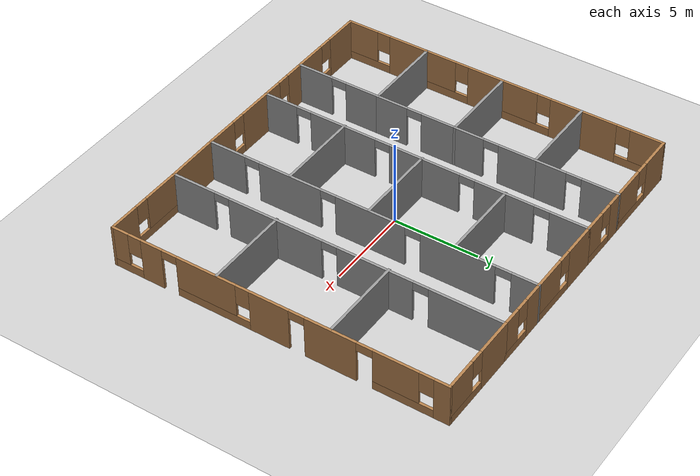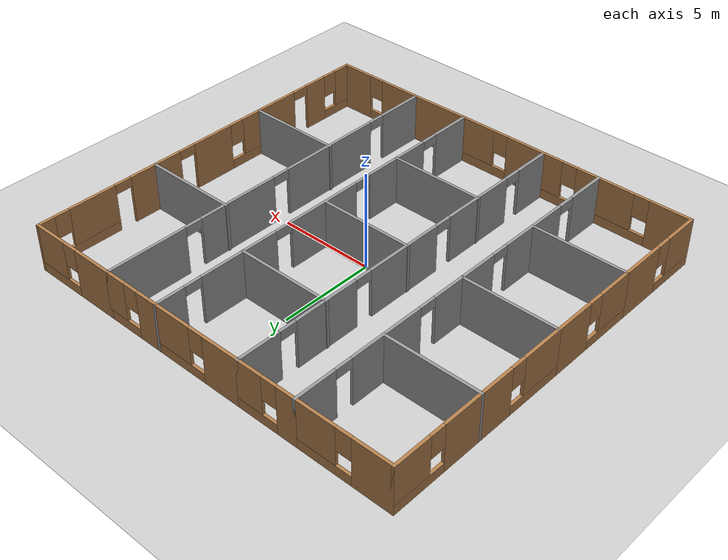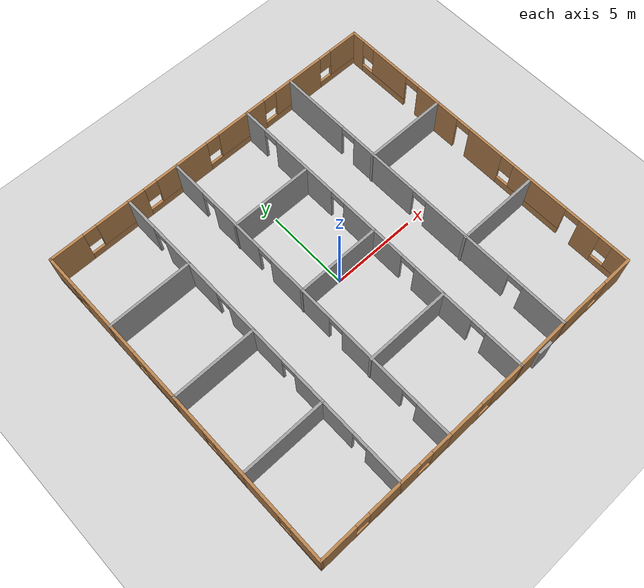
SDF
<sdf version="1.7">
  <world name="hospital_demo">
    <!-- ROS2 + Gazebo classic integration -->
    <plugin name="gazebo_ros_init" filename="libgazebo_ros_init.so"/>
    <plugin name="gazebo_ros_factory" filename="libgazebo_ros_factory.so"/>
    <plugin name="gazebo_ros_state" filename="libgazebo_ros_state.so"/>

    <gravity>0 0 -9.8</gravity>
    <physics type="ode">
      <max_step_size>0.001</max_step_size>
      <real_time_factor>1</real_time_factor>
      <real_time_update_rate>1000</real_time_update_rate>
    </physics>

    <scene>
      <ambient>0.4 0.4 0.4 1</ambient>
      <background>0.7 0.7 0.7 1</background>
      <shadows>1</shadows>
    </scene>

    <light name="sun" type="directional">
      <cast_shadows>1</cast_shadows>
      <pose>0 0 10 0 0 0</pose>
      <diffuse>0.8 0.8 0.8 1</diffuse>
      <specular>0.2 0.2 0.2 1</specular>
      <attenuation>
        <range>1000</range>
        <constant>0.9</constant>
        <linear>0.01</linear>
        <quadratic>0.001</quadratic>
      </attenuation>
      <direction>-0.5 0.1 -0.9</direction>
    </light>

    <model name="ground_plane">
      <static>1</static>
      <link name="link">
        <collision name="collision">
          <geometry>
            <plane>
              <normal>0 0 1</normal>
              <size>100 100</size>
            </plane>
          </geometry>
        </collision>
        <visual name="visual">
          <cast_shadows>0</cast_shadows>
          <geometry>
            <plane>
              <normal>0 0 1</normal>
              <size>100 100</size>
            </plane>
          </geometry>
          <material>
            <script>
              <uri>file://media/materials/scripts/gazebo.material</uri>
              <name>Gazebo/Grey</name>
            </script>
          </material>
        </visual>
      </link>
    </model>

    <!-- Hospital layout (walls/doors/rooms) -->
    <include>
      <uri>model://hospital_floor_v2</uri>
      <name>hospital_floor</name>
      <pose>0 0 0 0 0 0</pose>
    </include>
  </world>
</sdf>

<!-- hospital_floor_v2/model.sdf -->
<sdf version='1.7'>
  <model name='hospital_floor_v2'>
    <pose>-0.734547 -0.759195 0 0 -0 0</pose>
    <link name='Door_19'>
      <collision name='Door_19_Collision'>
        <geometry>
          <box>
            <size>0.9 0.17 2</size>
          </box>
        </geometry>
        <pose>0 0 1 0 -0 0</pose>
      </collision>
      <visual name='Door_19_Visual'>
        <pose>0 0 1 0 -0 0</pose>
        <geometry>
          <box>
            <size>0.9 0.17 2</size>
          </box>
        </geometry>
        <material>
          <script>
            <uri>file://media/materials/scripts/gazebo.material</uri>
            <name>Gazebo/Grey</name>
          </script>
        </material>
      </visual>
      <pose>4.12711 -9.93446 0 0 -0 0</pose>
    </link>
    <link name='Wall_111'>
      <pose>7.95 9.8256 0 0 -0 0</pose>
      <visual name='Wall_111_Visual_0'>
        <pose>-1.37417 0 1.25 0 -0 0</pose>
        <geometry>
          <box>
            <size>2.25167 0.15 2.5</size>
          </box>
        </geometry>
        <material>
          <script>
            <uri>file://media/materials/scripts/gazebo.material</uri>
            <name>Gazebo/Wood</name>
          </script>
          <ambient>1 1 1 1</ambient>
        </material>
        <meta>
          <layer>0</layer>
        </meta>
      </visual>
      <collision name='Wall_111_Collision_0'>
        <geometry>
          <box>
            <size>2.25167 0.15 2.5</size>
          </box>
        </geometry>
        <pose>-1.37417 0 1.25 0 -0 0</pose>
      </collision>
      <visual name='Wall_111_Visual_1'>
        <pose>1.12583 0 0.25 0 -0 0</pose>
        <geometry>
          <box>
            <size>2.74833 0.15 0.5</size>
          </box>
        </geometry>
        <material>
          <script>
            <uri>file://media/materials/scripts/gazebo.material</uri>
            <name>Gazebo/Wood</name>
          </script>
          <ambient>1 1 1 1</ambient>
        </material>
        <meta>
          <layer>0</layer>
        </meta>
      </visual>
      <collision name='Wall_111_Collision_1'>
        <geometry>
          <box>
            <size>2.74833 0.15 0.5</size>
          </box>
        </geometry>
        <pose>1.12583 0 0.25 0 -0 0</pose>
      </collision>
      <visual name='Wall_111_Visual_2'>
        <pose>1.52583 0 1.5 0 -0 0</pose>
        <geometry>
          <box>
            <size>1.94833 0.15 2</size>
          </box>
        </geometry>
        <material>
          <script>
            <uri>file://media/materials/scripts/gazebo.material</uri>
            <name>Gazebo/Wood</name>
          </script>
          <ambient>1 1 1 1</ambient>
        </material>
        <meta>
          <layer>0</layer>
        </meta>
      </visual>
      <collision name='Wall_111_Collision_2'>
        <geometry>
          <box>
            <size>1.94833 0.15 2</size>
          </box>
        </geometry>
        <pose>1.52583 0 1.5 0 -0 0</pose>
      </collision>
      <visual name='Wall_111_Visual_3'>
        <pose>0.151665 0 1.9 0 -0 0</pose>
        <geometry>
          <box>
            <size>0.8 0.15 1.2</size>
          </box>
        </geometry>
        <material>
          <script>
            <uri>file://media/materials/scripts/gazebo.material</uri>
            <name>Gazebo/Wood</name>
          </script>
          <ambient>1 1 1 1</ambient>
        </material>
        <meta>
          <layer>0</layer>
        </meta>
      </visual>
      <collision name='Wall_111_Collision_3'>
        <geometry>
          <box>
            <size>0.8 0.15 1.2</size>
          </box>
        </geometry>
        <pose>0.151665 0 1.9 0 -0 0</pose>
      </collision>
    </link>
    <link name='Wall_112'>
      <pose>10.375 0.025599 0 0 -0 -1.5708</pose>
      <visual name='Wall_112_Visual_0'>
        <pose>-9.42467 0 1.25 0 -0 0</pose>
        <geometry>
          <box>
            <size>0.900667 0.15 2.5</size>
          </box>
        </geometry>
        <material>
          <script>
            <uri>file://media/materials/scripts/gazebo.material</uri>
            <name>Gazebo/Wood</name>
          </script>
          <ambient>1 1 1 1</ambient>
        </material>
        <meta>
          <layer>0</layer>
        </meta>
      </visual>
      <collision name='Wall_112_Collision_0'>
        <geometry>
          <box>
            <size>0.900667 0.15 2.5</size>
          </box>
        </geometry>
        <pose>-9.42467 0 1.25 0 -0 0</pose>
      </collision>
      <visual name='Wall_112_Visual_1'>
        <pose>-3.24113 0 1.25 0 -0 0</pose>
        <geometry>
          <box>
            <size>2.95288 0.15 2.5</size>
          </box>
        </geometry>
        <material>
          <script>
            <uri>file://media/materials/scripts/gazebo.material</uri>
            <name>Gazebo/Wood</name>
          </script>
          <ambient>1 1 1 1</ambient>
        </material>
        <meta>
          <layer>0</layer>
        </meta>
      </visual>
      <collision name='Wall_112_Collision_1'>
        <geometry>
          <box>
            <size>2.95288 0.15 2.5</size>
          </box>
        </geometry>
        <pose>-3.24113 0 1.25 0 -0 0</pose>
      </collision>
      <visual name='Wall_112_Visual_2'>
        <pose>0.29202 0 1.25 0 -0 0</pose>
        <geometry>
          <box>
            <size>2.31342 0.15 2.5</size>
          </box>
        </geometry>
        <material>
          <script>
            <uri>file://media/materials/scripts/gazebo.material</uri>
            <name>Gazebo/Wood</name>
          </script>
          <ambient>1 1 1 1</ambient>
        </material>
        <meta>
          <layer>0</layer>
        </meta>
      </visual>
      <collision name='Wall_112_Collision_2'>
        <geometry>
          <box>
            <size>2.31342 0.15 2.5</size>
          </box>
        </geometry>
        <pose>0.29202 0 1.25 0 -0 0</pose>
      </collision>
      <visual name='Wall_112_Visual_3'>
        <pose>7.36916 0 1.25 0 -0 0</pose>
        <geometry>
          <box>
            <size>1.2995 0.15 2.5</size>
          </box>
        </geometry>
        <material>
          <script>
            <uri>file://media/materials/scripts/gazebo.material</uri>
            <name>Gazebo/Wood</name>
          </script>
          <ambient>1 1 1 1</ambient>
        </material>
        <meta>
          <layer>0</layer>
        </meta>
      </visual>
      <collision name='Wall_112_Collision_3'>
        <geometry>
          <box>
            <size>1.2995 0.15 2.5</size>
          </box>
        </geometry>
        <pose>7.36916 0 1.25 0 -0 0</pose>
      </collision>
      <visual name='Wall_112_Visual_4'>
        <pose>-7.29595 0 0.25 0 -0 0</pose>
        <geometry>
          <box>
            <size>3.35676 0.15 0.5</size>
          </box>
        </geometry>
        <material>
          <script>
            <uri>file://media/materials/scripts/gazebo.material</uri>
            <name>Gazebo/Wood</name>
          </script>
          <ambient>1 1 1 1</ambient>
        </material>
        <meta>
          <layer>0</layer>
        </meta>
      </visual>
      <collision name='Wall_112_Collision_4'>
        <geometry>
          <box>
            <size>3.35676 0.15 0.5</size>
          </box>
        </geometry>
        <pose>-7.29595 0 0.25 0 -0 0</pose>
      </collision>
      <visual name='Wall_112_Visual_5'>
        <pose>3.63407 0 0.25 0 -0 0</pose>
        <geometry>
          <box>
            <size>4.37068 0.15 0.5</size>
          </box>
        </geometry>
        <material>
          <script>
            <uri>file://media/materials/scripts/gazebo.material</uri>
            <name>Gazebo/Wood</name>
          </script>
          <ambient>1 1 1 1</ambient>
        </material>
        <meta>
          <layer>0</layer>
        </meta>
      </visual>
      <collision name='Wall_112_Collision_5'>
        <geometry>
          <box>
            <size>4.37068 0.15 0.5</size>
          </box>
        </geometry>
        <pose>3.63407 0 0.25 0 -0 0</pose>
      </collision>
      <visual name='Wall_112_Visual_6'>
        <pose>8.94696 0 0.25 0 -0 0</pose>
        <geometry>
          <box>
            <size>1.85609 0.15 0.5</size>
          </box>
        </geometry>
        <material>
          <script>
            <uri>file://media/materials/scripts/gazebo.material</uri>
            <name>Gazebo/Wood</name>
          </script>
          <ambient>1 1 1 1</ambient>
        </material>
        <meta>
          <layer>0</layer>
        </meta>
      </visual>
      <collision name='Wall_112_Collision_6'>
        <geometry>
          <box>
            <size>1.85609 0.15 0.5</size>
          </box>
        </geometry>
        <pose>8.94696 0 0.25 0 -0 0</pose>
      </collision>
      <visual name='Wall_112_Visual_7'>
        <pose>-6.89595 0 1.5 0 -0 0</pose>
        <geometry>
          <box>
            <size>2.55676 0.15 2</size>
          </box>
        </geometry>
        <material>
          <script>
            <uri>file://media/materials/scripts/gazebo.material</uri>
            <name>Gazebo/Wood</name>
          </script>
          <ambient>1 1 1 1</ambient>
        </material>
        <meta>
          <layer>0</layer>
        </meta>
      </visual>
      <collision name='Wall_112_Collision_7'>
        <geometry>
          <box>
            <size>2.55676 0.15 2</size>
          </box>
        </geometry>
        <pose>-6.89595 0 1.5 0 -0 0</pose>
      </collision>
      <visual name='Wall_112_Visual_8'>
        <pose>-6.89595 0 1.5 0 -0 0</pose>
        <geometry>
          <box>
            <size>2.55676 0.15 2</size>
          </box>
        </geometry>
        <material>
          <script>
            <uri>file://media/materials/scripts/gazebo.material</uri>
            <name>Gazebo/Wood</name>
          </script>
          <ambient>1 1 1 1</ambient>
        </material>
        <meta>
          <layer>0</layer>
        </meta>
      </visual>
      <collision name='Wall_112_Collision_8'>
        <geometry>
          <box>
            <size>2.55676 0.15 2</size>
          </box>
        </geometry>
        <pose>-6.89595 0 1.5 0 -0 0</pose>
      </collision>
      <visual name='Wall_112_Visual_9'>
        <pose>4.03407 0 1.5 0 -0 0</pose>
        <geometry>
          <box>
            <size>3.57068 0.15 2</size>
          </box>
        </geometry>
        <material>
          <script>
            <uri>file://media/materials/scripts/gazebo.material</uri>
            <name>Gazebo/Wood</name>
          </script>
          <ambient>1 1 1 1</ambient>
        </material>
        <meta>
          <layer>0</layer>
        </meta>
      </visual>
      <collision name='Wall_112_Collision_9'>
        <geometry>
          <box>
            <size>3.57068 0.15 2</size>
          </box>
        </geometry>
        <pose>4.03407 0 1.5 0 -0 0</pose>
      </collision>
      <visual name='Wall_112_Visual_10'>
        <pose>4.03407 0 1.5 0 -0 0</pose>
        <geometry>
          <box>
            <size>3.57068 0.15 2</size>
          </box>
        </geometry>
        <material>
          <script>
            <uri>file://media/materials/scripts/gazebo.material</uri>
            <name>Gazebo/Wood</name>
          </script>
          <ambient>1 1 1 1</ambient>
        </material>
        <meta>
          <layer>0</layer>
        </meta>
      </visual>
      <collision name='Wall_112_Collision_10'>
        <geometry>
          <box>
            <size>3.57068 0.15 2</size>
          </box>
        </geometry>
        <pose>4.03407 0 1.5 0 -0 0</pose>
      </collision>
      <visual name='Wall_112_Visual_11'>
        <pose>9.34695 0 1.5 0 -0 0</pose>
        <geometry>
          <box>
            <size>1.05609 0.15 2</size>
          </box>
        </geometry>
        <material>
          <script>
            <uri>file://media/materials/scripts/gazebo.material</uri>
            <name>Gazebo/Wood</name>
          </script>
          <ambient>1 1 1 1</ambient>
        </material>
        <meta>
          <layer>0</layer>
        </meta>
      </visual>
      <collision name='Wall_112_Collision_11'>
        <geometry>
          <box>
            <size>1.05609 0.15 2</size>
          </box>
        </geometry>
        <pose>9.34695 0 1.5 0 -0 0</pose>
      </collision>
      <visual name='Wall_112_Visual_12'>
        <pose>-8.57433 0 1.9 0 -0 0</pose>
        <geometry>
          <box>
            <size>0.8 0.15 1.2</size>
          </box>
        </geometry>
        <material>
          <script>
            <uri>file://media/materials/scripts/gazebo.material</uri>
            <name>Gazebo/Wood</name>
          </script>
          <ambient>1 1 1 1</ambient>
        </material>
        <meta>
          <layer>0</layer>
        </meta>
      </visual>
      <collision name='Wall_112_Collision_12'>
        <geometry>
          <box>
            <size>0.8 0.15 1.2</size>
          </box>
        </geometry>
        <pose>-8.57433 0 1.9 0 -0 0</pose>
      </collision>
      <visual name='Wall_112_Visual_13'>
        <pose>1.84873 0 1.9 0 -0 0</pose>
        <geometry>
          <box>
            <size>0.8 0.15 1.2</size>
          </box>
        </geometry>
        <material>
          <script>
            <uri>file://media/materials/scripts/gazebo.material</uri>
            <name>Gazebo/Wood</name>
          </script>
          <ambient>1 1 1 1</ambient>
        </material>
        <meta>
          <layer>0</layer>
        </meta>
      </visual>
      <collision name='Wall_112_Collision_13'>
        <geometry>
          <box>
            <size>0.8 0.15 1.2</size>
          </box>
        </geometry>
        <pose>1.84873 0 1.9 0 -0 0</pose>
      </collision>
      <visual name='Wall_112_Visual_14'>
        <pose>8.41891 0 1.9 0 -0 0</pose>
        <geometry>
          <box>
            <size>0.8 0.15 1.2</size>
          </box>
        </geometry>
        <material>
          <script>
            <uri>file://media/materials/scripts/gazebo.material</uri>
            <name>Gazebo/Wood</name>
          </script>
          <ambient>1 1 1 1</ambient>
        </material>
        <meta>
          <layer>0</layer>
        </meta>
      </visual>
      <collision name='Wall_112_Collision_14'>
        <geometry>
          <box>
            <size>0.8 0.15 1.2</size>
          </box>
        </geometry>
        <pose>8.41891 0 1.9 0 -0 0</pose>
      </collision>
      <visual name='Wall_112_Visual_15'>
        <pose>-1.31469 0 2.25 0 -0 0</pose>
        <geometry>
          <box>
            <size>0.9 0.15 0.5</size>
          </box>
        </geometry>
        <material>
          <script>
            <uri>file://media/materials/scripts/gazebo.material</uri>
            <name>Gazebo/Wood</name>
          </script>
          <ambient>1 1 1 1</ambient>
        </material>
        <meta>
          <layer>0</layer>
        </meta>
      </visual>
      <collision name='Wall_112_Collision_15'>
        <geometry>
          <box>
            <size>0.9 0.15 0.5</size>
          </box>
        </geometry>
        <pose>-1.31469 0 2.25 0 -0 0</pose>
      </collision>
      <visual name='Wall_112_Visual_16'>
        <pose>-5.16757 0 2.25 0 -0 0</pose>
        <geometry>
          <box>
            <size>0.9 0.15 0.5</size>
          </box>
        </geometry>
        <material>
          <script>
            <uri>file://media/materials/scripts/gazebo.material</uri>
            <name>Gazebo/Wood</name>
          </script>
          <ambient>1 1 1 1</ambient>
        </material>
        <meta>
          <layer>0</layer>
        </meta>
      </visual>
      <collision name='Wall_112_Collision_16'>
        <geometry>
          <box>
            <size>0.9 0.15 0.5</size>
          </box>
        </geometry>
        <pose>-5.16757 0 2.25 0 -0 0</pose>
      </collision>
      <visual name='Wall_112_Visual_17'>
        <pose>-5.16757 0 2.25 0 -0 0</pose>
        <geometry>
          <box>
            <size>0.9 0.15 0.5</size>
          </box>
        </geometry>
        <material>
          <script>
            <uri>file://media/materials/scripts/gazebo.material</uri>
            <name>Gazebo/Wood</name>
          </script>
          <ambient>1 1 1 1</ambient>
        </material>
        <meta>
          <layer>0</layer>
        </meta>
      </visual>
      <collision name='Wall_112_Collision_17'>
        <geometry>
          <box>
            <size>0.9 0.15 0.5</size>
          </box>
        </geometry>
        <pose>-5.16757 0 2.25 0 -0 0</pose>
      </collision>
      <visual name='Wall_112_Visual_18'>
        <pose>6.26941 0 2.25 0 -0 0</pose>
        <geometry>
          <box>
            <size>0.9 0.15 0.5</size>
          </box>
        </geometry>
        <material>
          <script>
            <uri>file://media/materials/scripts/gazebo.material</uri>
            <name>Gazebo/Wood</name>
          </script>
          <ambient>1 1 1 1</ambient>
        </material>
        <meta>
          <layer>0</layer>
        </meta>
      </visual>
      <collision name='Wall_112_Collision_18'>
        <geometry>
          <box>
            <size>0.9 0.15 0.5</size>
          </box>
        </geometry>
        <pose>6.26941 0 2.25 0 -0 0</pose>
      </collision>
      <visual name='Wall_112_Visual_19'>
        <pose>6.26941 0 2.25 0 -0 0</pose>
        <geometry>
          <box>
            <size>0.9 0.15 0.5</size>
          </box>
        </geometry>
        <material>
          <script>
            <uri>file://media/materials/scripts/gazebo.material</uri>
            <name>Gazebo/Wood</name>
          </script>
          <ambient>1 1 1 1</ambient>
        </material>
        <meta>
          <layer>0</layer>
        </meta>
      </visual>
      <collision name='Wall_112_Collision_19'>
        <geometry>
          <box>
            <size>0.9 0.15 0.5</size>
          </box>
        </geometry>
        <pose>6.26941 0 2.25 0 -0 0</pose>
      </collision>
    </link>
    <link name='Wall_113'>
      <pose>7.95 -9.7744 0 0 -0 3.14159</pose>
      <visual name='Wall_113_Visual_0'>
        <pose>-1.56639 0 1.25 0 -0 0</pose>
        <geometry>
          <box>
            <size>1.86722 0.15 2.5</size>
          </box>
        </geometry>
        <material>
          <script>
            <uri>file://media/materials/scripts/gazebo.material</uri>
            <name>Gazebo/Wood</name>
          </script>
          <ambient>1 1 1 1</ambient>
        </material>
        <meta>
          <layer>0</layer>
        </meta>
      </visual>
      <collision name='Wall_113_Collision_0'>
        <geometry>
          <box>
            <size>1.86722 0.15 2.5</size>
          </box>
        </geometry>
        <pose>-1.56639 0 1.25 0 -0 0</pose>
      </collision>
      <visual name='Wall_113_Visual_1'>
        <pose>0.933611 0 0.25 0 -0 0</pose>
        <geometry>
          <box>
            <size>3.13278 0.15 0.5</size>
          </box>
        </geometry>
        <material>
          <script>
            <uri>file://media/materials/scripts/gazebo.material</uri>
            <name>Gazebo/Wood</name>
          </script>
          <ambient>1 1 1 1</ambient>
        </material>
        <meta>
          <layer>0</layer>
        </meta>
      </visual>
      <collision name='Wall_113_Collision_1'>
        <geometry>
          <box>
            <size>3.13278 0.15 0.5</size>
          </box>
        </geometry>
        <pose>0.933611 0 0.25 0 -0 0</pose>
      </collision>
      <visual name='Wall_113_Visual_2'>
        <pose>1.33361 0 1.5 0 -0 0</pose>
        <geometry>
          <box>
            <size>2.33278 0.15 2</size>
          </box>
        </geometry>
        <material>
          <script>
            <uri>file://media/materials/scripts/gazebo.material</uri>
            <name>Gazebo/Wood</name>
          </script>
          <ambient>1 1 1 1</ambient>
        </material>
        <meta>
          <layer>0</layer>
        </meta>
      </visual>
      <collision name='Wall_113_Collision_2'>
        <geometry>
          <box>
            <size>2.33278 0.15 2</size>
          </box>
        </geometry>
        <pose>1.33361 0 1.5 0 -0 0</pose>
      </collision>
      <visual name='Wall_113_Visual_3'>
        <pose>-0.232779 0 1.9 0 -0 0</pose>
        <geometry>
          <box>
            <size>0.8 0.15 1.2</size>
          </box>
        </geometry>
        <material>
          <script>
            <uri>file://media/materials/scripts/gazebo.material</uri>
            <name>Gazebo/Wood</name>
          </script>
          <ambient>1 1 1 1</ambient>
        </material>
        <meta>
          <layer>0</layer>
        </meta>
      </visual>
      <collision name='Wall_113_Collision_3'>
        <geometry>
          <box>
            <size>0.8 0.15 1.2</size>
          </box>
        </geometry>
        <pose>-0.232779 0 1.9 0 -0 0</pose>
      </collision>
    </link>
    <link name='Wall_115'>
      <collision name='Wall_115_Collision'>
        <geometry>
          <box>
            <size>5 0.15 2.5</size>
          </box>
        </geometry>
        <pose>0 0 1.25 0 -0 0</pose>
      </collision>
      <visual name='Wall_115_Visual'>
        <pose>0 0 1.25 0 -0 0</pose>
        <geometry>
          <box>
            <size>5 0.15 2.5</size>
          </box>
        </geometry>
        <material>
          <script>
            <uri>file://media/materials/scripts/gazebo.material</uri>
            <name>Gazebo/Grey</name>
          </script>
          <ambient>1 1 1 1</ambient>
        </material>
        <meta>
          <layer>0</layer>
        </meta>
      </visual>
      <pose>-0.036828 5.04089 0 0 -0 0</pose>
    </link>
    <link name='Wall_117'>
      <collision name='Wall_117_Collision'>
        <geometry>
          <box>
            <size>5 0.15 2.5</size>
          </box>
        </geometry>
        <pose>0 0 1.25 0 -0 0</pose>
      </collision>
      <visual name='Wall_117_Visual'>
        <pose>0 0 1.25 0 -0 0</pose>
        <geometry>
          <box>
            <size>5 0.15 2.5</size>
          </box>
        </geometry>
        <material>
          <script>
            <uri>file://media/materials/scripts/gazebo.material</uri>
            <name>Gazebo/Grey</name>
          </script>
          <ambient>1 1 1 1</ambient>
        </material>
        <meta>
          <layer>0</layer>
        </meta>
      </visual>
      <pose>-0.036828 0.052719 0 0 -0 0</pose>
    </link>
    <link name='Wall_119'>
      <collision name='Wall_119_Collision'>
        <geometry>
          <box>
            <size>5 0.15 2.5</size>
          </box>
        </geometry>
        <pose>0 0 1.25 0 -0 0</pose>
      </collision>
      <visual name='Wall_119_Visual'>
        <pose>0 0 1.25 0 -0 0</pose>
        <geometry>
          <box>
            <size>5 0.15 2.5</size>
          </box>
        </geometry>
        <material>
          <script>
            <uri>file://media/materials/scripts/gazebo.material</uri>
            <name>Gazebo/Grey</name>
          </script>
          <ambient>1 1 1 1</ambient>
        </material>
        <meta>
          <layer>0</layer>
        </meta>
      </visual>
      <pose>-0.036828 -4.77454 0 0 -0 0</pose>
    </link>
    <link name='Wall_123'>
      <collision name='Wall_123_Collision'>
        <geometry>
          <box>
            <size>5 0.15 2.5</size>
          </box>
        </geometry>
        <pose>0 0 1.25 0 -0 0</pose>
      </collision>
      <visual name='Wall_123_Visual'>
        <pose>0 0 1.25 0 -0 0</pose>
        <geometry>
          <box>
            <size>5 0.15 2.5</size>
          </box>
        </geometry>
        <material>
          <script>
            <uri>file://media/materials/scripts/gazebo.material</uri>
            <name>Gazebo/Grey</name>
          </script>
          <ambient>1 1 1 1</ambient>
        </material>
        <meta>
          <layer>0</layer>
        </meta>
      </visual>
      <pose>7.90133 3.27089 0 0 -0 0</pose>
    </link>
    <link name='Wall_125'>
      <collision name='Wall_125_Collision'>
        <geometry>
          <box>
            <size>5 0.15 2.5</size>
          </box>
        </geometry>
        <pose>0 0 1.25 0 -0 0</pose>
      </collision>
      <visual name='Wall_125_Visual'>
        <pose>0 0 1.25 0 -0 0</pose>
        <geometry>
          <box>
            <size>5 0.15 2.5</size>
          </box>
        </geometry>
        <material>
          <script>
            <uri>file://media/materials/scripts/gazebo.material</uri>
            <name>Gazebo/Grey</name>
          </script>
          <ambient>1 1 1 1</ambient>
        </material>
        <meta>
          <layer>0</layer>
        </meta>
      </visual>
      <pose>7.90133 -3.38 0 0 -0 0</pose>
    </link>
    <link name='Wall_24'>
      <pose>-10.375 2.5506 0 0 -0 -1.5708</pose>
      <visual name='Wall_24_Visual_0'>
        <pose>-1.53431 0 1.25 0 -0 0</pose>
        <geometry>
          <box>
            <size>1.93138 0.15 2.5</size>
          </box>
        </geometry>
        <material>
          <script>
            <uri>file://media/materials/scripts/gazebo.material</uri>
            <name>Gazebo/Wood</name>
          </script>
          <ambient>1 1 1 1</ambient>
        </material>
        <meta>
          <layer>0</layer>
        </meta>
      </visual>
      <collision name='Wall_24_Collision_0'>
        <geometry>
          <box>
            <size>1.93138 0.15 2.5</size>
          </box>
        </geometry>
        <pose>-1.53431 0 1.25 0 -0 0</pose>
      </collision>
      <visual name='Wall_24_Visual_1'>
        <pose>0.965692 0 0.25 0 -0 0</pose>
        <geometry>
          <box>
            <size>3.06862 0.15 0.5</size>
          </box>
        </geometry>
        <material>
          <script>
            <uri>file://media/materials/scripts/gazebo.material</uri>
            <name>Gazebo/Wood</name>
          </script>
          <ambient>1 1 1 1</ambient>
        </material>
        <meta>
          <layer>0</layer>
        </meta>
      </visual>
      <collision name='Wall_24_Collision_1'>
        <geometry>
          <box>
            <size>3.06862 0.15 0.5</size>
          </box>
        </geometry>
        <pose>0.965692 0 0.25 0 -0 0</pose>
      </collision>
      <visual name='Wall_24_Visual_2'>
        <pose>1.36569 0 1.5 0 -0 0</pose>
        <geometry>
          <box>
            <size>2.26862 0.15 2</size>
          </box>
        </geometry>
        <material>
          <script>
            <uri>file://media/materials/scripts/gazebo.material</uri>
            <name>Gazebo/Wood</name>
          </script>
          <ambient>1 1 1 1</ambient>
        </material>
        <meta>
          <layer>0</layer>
        </meta>
      </visual>
      <collision name='Wall_24_Collision_2'>
        <geometry>
          <box>
            <size>2.26862 0.15 2</size>
          </box>
        </geometry>
        <pose>1.36569 0 1.5 0 -0 0</pose>
      </collision>
      <visual name='Wall_24_Visual_3'>
        <pose>-0.168617 0 1.9 0 -0 0</pose>
        <geometry>
          <box>
            <size>0.8 0.15 1.2</size>
          </box>
        </geometry>
        <material>
          <script>
            <uri>file://media/materials/scripts/gazebo.material</uri>
            <name>Gazebo/Wood</name>
          </script>
          <ambient>1 1 1 1</ambient>
        </material>
        <meta>
          <layer>0</layer>
        </meta>
      </visual>
      <collision name='Wall_24_Collision_3'>
        <geometry>
          <box>
            <size>0.8 0.15 1.2</size>
          </box>
        </geometry>
        <pose>-0.168617 0 1.9 0 -0 0</pose>
      </collision>
    </link>
    <link name='Wall_28'>
      <collision name='Wall_28_Collision'>
        <geometry>
          <box>
            <size>5 0.15 2.5</size>
          </box>
        </geometry>
        <pose>0 0 1.25 0 -0 0</pose>
      </collision>
      <visual name='Wall_28_Visual'>
        <pose>0 0 1.25 0 -0 0</pose>
        <geometry>
          <box>
            <size>5 0.15 2.5</size>
          </box>
        </geometry>
        <material>
          <script>
            <uri>file://media/materials/scripts/gazebo.material</uri>
            <name>Gazebo/Grey</name>
          </script>
          <ambient>1 1 1 1</ambient>
        </material>
        <meta>
          <layer>0</layer>
        </meta>
      </visual>
      <pose>-7.95 4.9756 0 0 -0 0</pose>
    </link>
    <link name='Wall_29'>
      <pose>-5.525 2.5506 0 0 -0 -1.5708</pose>
      <visual name='Wall_29_Visual_0'>
        <pose>-1.3768 0 1.25 0 -0 0</pose>
        <geometry>
          <box>
            <size>2.24639 0.15 2.5</size>
          </box>
        </geometry>
        <material>
          <script>
            <uri>file://media/materials/scripts/gazebo.material</uri>
            <name>Gazebo/Grey</name>
          </script>
          <ambient>1 1 1 1</ambient>
        </material>
        <meta>
          <layer>0</layer>
        </meta>
      </visual>
      <collision name='Wall_29_Collision_0'>
        <geometry>
          <box>
            <size>2.24639 0.15 2.5</size>
          </box>
        </geometry>
        <pose>-1.3768 0 1.25 0 -0 0</pose>
      </collision>
      <visual name='Wall_29_Visual_1'>
        <pose>1.5732 0 1.25 0 -0 0</pose>
        <geometry>
          <box>
            <size>1.85361 0.15 2.5</size>
          </box>
        </geometry>
        <material>
          <script>
            <uri>file://media/materials/scripts/gazebo.material</uri>
            <name>Gazebo/Grey</name>
          </script>
          <ambient>1 1 1 1</ambient>
        </material>
        <meta>
          <layer>0</layer>
        </meta>
      </visual>
      <collision name='Wall_29_Collision_1'>
        <geometry>
          <box>
            <size>1.85361 0.15 2.5</size>
          </box>
        </geometry>
        <pose>1.5732 0 1.25 0 -0 0</pose>
      </collision>
      <visual name='Wall_29_Visual_2'>
        <pose>0.196393 0 2.25 0 -0 0</pose>
        <geometry>
          <box>
            <size>0.9 0.15 0.5</size>
          </box>
        </geometry>
        <material>
          <script>
            <uri>file://media/materials/scripts/gazebo.material</uri>
            <name>Gazebo/Grey</name>
          </script>
          <ambient>1 1 1 1</ambient>
        </material>
        <meta>
          <layer>0</layer>
        </meta>
      </visual>
      <collision name='Wall_29_Collision_2'>
        <geometry>
          <box>
            <size>0.9 0.15 0.5</size>
          </box>
        </geometry>
        <pose>0.196393 0 2.25 0 -0 0</pose>
      </collision>
    </link>
    <link name='Wall_30'>
      <collision name='Wall_30_Collision'>
        <geometry>
          <box>
            <size>5 0.15 2.5</size>
          </box>
        </geometry>
        <pose>0 0 1.25 0 -0 0</pose>
      </collision>
      <visual name='Wall_30_Visual'>
        <pose>0 0 1.25 0 -0 0</pose>
        <geometry>
          <box>
            <size>5 0.15 2.5</size>
          </box>
        </geometry>
        <material>
          <script>
            <uri>file://media/materials/scripts/gazebo.material</uri>
            <name>Gazebo/Grey</name>
          </script>
          <ambient>1 1 1 1</ambient>
        </material>
        <meta>
          <layer>0</layer>
        </meta>
      </visual>
      <pose>-7.95 0.125599 0 0 -0 3.14159</pose>
    </link>
    <link name='Wall_31'>
      <pose>-10.375 -2.2994 0 0 -0 -1.5708</pose>
      <visual name='Wall_31_Visual_0'>
        <pose>-1.38396 0 1.25 0 -0 0</pose>
        <geometry>
          <box>
            <size>2.23208 0.15 2.5</size>
          </box>
        </geometry>
        <material>
          <script>
            <uri>file://media/materials/scripts/gazebo.material</uri>
            <name>Gazebo/Wood</name>
          </script>
          <ambient>1 1 1 1</ambient>
        </material>
        <meta>
          <layer>0</layer>
        </meta>
      </visual>
      <collision name='Wall_31_Collision_0'>
        <geometry>
          <box>
            <size>2.23208 0.15 2.5</size>
          </box>
        </geometry>
        <pose>-1.38396 0 1.25 0 -0 0</pose>
      </collision>
      <visual name='Wall_31_Visual_1'>
        <pose>1.11604 0 0.25 0 -0 0</pose>
        <geometry>
          <box>
            <size>2.76792 0.15 0.5</size>
          </box>
        </geometry>
        <material>
          <script>
            <uri>file://media/materials/scripts/gazebo.material</uri>
            <name>Gazebo/Wood</name>
          </script>
          <ambient>1 1 1 1</ambient>
        </material>
        <meta>
          <layer>0</layer>
        </meta>
      </visual>
      <collision name='Wall_31_Collision_1'>
        <geometry>
          <box>
            <size>2.76792 0.15 0.5</size>
          </box>
        </geometry>
        <pose>1.11604 0 0.25 0 -0 0</pose>
      </collision>
      <visual name='Wall_31_Visual_2'>
        <pose>1.51604 0 1.5 0 -0 0</pose>
        <geometry>
          <box>
            <size>1.96792 0.15 2</size>
          </box>
        </geometry>
        <material>
          <script>
            <uri>file://media/materials/scripts/gazebo.material</uri>
            <name>Gazebo/Wood</name>
          </script>
          <ambient>1 1 1 1</ambient>
        </material>
        <meta>
          <layer>0</layer>
        </meta>
      </visual>
      <collision name='Wall_31_Collision_2'>
        <geometry>
          <box>
            <size>1.96792 0.15 2</size>
          </box>
        </geometry>
        <pose>1.51604 0 1.5 0 -0 0</pose>
      </collision>
      <visual name='Wall_31_Visual_3'>
        <pose>0.13208 0 1.9 0 -0 0</pose>
        <geometry>
          <box>
            <size>0.8 0.15 1.2</size>
          </box>
        </geometry>
        <material>
          <script>
            <uri>file://media/materials/scripts/gazebo.material</uri>
            <name>Gazebo/Wood</name>
          </script>
          <ambient>1 1 1 1</ambient>
        </material>
        <meta>
          <layer>0</layer>
        </meta>
      </visual>
      <collision name='Wall_31_Collision_3'>
        <geometry>
          <box>
            <size>0.8 0.15 1.2</size>
          </box>
        </geometry>
        <pose>0.13208 0 1.9 0 -0 0</pose>
      </collision>
    </link>
    <link name='Wall_32'>
      <collision name='Wall_32_Collision'>
        <geometry>
          <box>
            <size>5 0.15 2.5</size>
          </box>
        </geometry>
        <pose>0 0 1.25 0 -0 0</pose>
      </collision>
      <visual name='Wall_32_Visual'>
        <pose>0 0 1.25 0 -0 0</pose>
        <geometry>
          <box>
            <size>5 0.15 2.5</size>
          </box>
        </geometry>
        <material>
          <script>
            <uri>file://media/materials/scripts/gazebo.material</uri>
            <name>Gazebo/Grey</name>
          </script>
          <ambient>1 1 1 1</ambient>
        </material>
        <meta>
          <layer>0</layer>
        </meta>
      </visual>
      <pose>-7.95 -4.7244 0 0 -0 0</pose>
    </link>
    <link name='Wall_33'>
      <pose>-5.525 -2.2994 0 0 -0 1.5708</pose>
      <visual name='Wall_33_Visual_0'>
        <pose>-1.52076 0 1.25 0 -0 0</pose>
        <geometry>
          <box>
            <size>1.95848 0.15 2.5</size>
          </box>
        </geometry>
        <material>
          <script>
            <uri>file://media/materials/scripts/gazebo.material</uri>
            <name>Gazebo/Grey</name>
          </script>
          <ambient>1 1 1 1</ambient>
        </material>
        <meta>
          <layer>0</layer>
        </meta>
      </visual>
      <collision name='Wall_33_Collision_0'>
        <geometry>
          <box>
            <size>1.95848 0.15 2.5</size>
          </box>
        </geometry>
        <pose>-1.52076 0 1.25 0 -0 0</pose>
      </collision>
      <visual name='Wall_33_Visual_1'>
        <pose>1.42924 0 1.25 0 -0 0</pose>
        <geometry>
          <box>
            <size>2.14152 0.15 2.5</size>
          </box>
        </geometry>
        <material>
          <script>
            <uri>file://media/materials/scripts/gazebo.material</uri>
            <name>Gazebo/Grey</name>
          </script>
          <ambient>1 1 1 1</ambient>
        </material>
        <meta>
          <layer>0</layer>
        </meta>
      </visual>
      <collision name='Wall_33_Collision_1'>
        <geometry>
          <box>
            <size>2.14152 0.15 2.5</size>
          </box>
        </geometry>
        <pose>1.42924 0 1.25 0 -0 0</pose>
      </collision>
      <visual name='Wall_33_Visual_2'>
        <pose>-0.091523 0 2.25 0 -0 0</pose>
        <geometry>
          <box>
            <size>0.9 0.15 0.5</size>
          </box>
        </geometry>
        <material>
          <script>
            <uri>file://media/materials/scripts/gazebo.material</uri>
            <name>Gazebo/Grey</name>
          </script>
          <ambient>1 1 1 1</ambient>
        </material>
        <meta>
          <layer>0</layer>
        </meta>
      </visual>
      <collision name='Wall_33_Collision_2'>
        <geometry>
          <box>
            <size>0.9 0.15 0.5</size>
          </box>
        </geometry>
        <pose>-0.091523 0 2.25 0 -0 0</pose>
      </collision>
    </link>
    <link name='Wall_35'>
      <pose>-10.375 -7.2744 0 0 -0 -1.5708</pose>
      <visual name='Wall_35_Visual_0'>
        <pose>-1.37889 0 1.25 0 -0 0</pose>
        <geometry>
          <box>
            <size>2.49222 0.15 2.5</size>
          </box>
        </geometry>
        <material>
          <script>
            <uri>file://media/materials/scripts/gazebo.material</uri>
            <name>Gazebo/Wood</name>
          </script>
          <ambient>1 1 1 1</ambient>
        </material>
        <meta>
          <layer>0</layer>
        </meta>
      </visual>
      <collision name='Wall_35_Collision_0'>
        <geometry>
          <box>
            <size>2.49222 0.15 2.5</size>
          </box>
        </geometry>
        <pose>-1.37889 0 1.25 0 -0 0</pose>
      </collision>
      <visual name='Wall_35_Visual_1'>
        <pose>1.24611 0 0.25 0 -0 0</pose>
        <geometry>
          <box>
            <size>2.75778 0.15 0.5</size>
          </box>
        </geometry>
        <material>
          <script>
            <uri>file://media/materials/scripts/gazebo.material</uri>
            <name>Gazebo/Wood</name>
          </script>
          <ambient>1 1 1 1</ambient>
        </material>
        <meta>
          <layer>0</layer>
        </meta>
      </visual>
      <collision name='Wall_35_Collision_1'>
        <geometry>
          <box>
            <size>2.75778 0.15 0.5</size>
          </box>
        </geometry>
        <pose>1.24611 0 0.25 0 -0 0</pose>
      </collision>
      <visual name='Wall_35_Visual_2'>
        <pose>1.64611 0 1.5 0 -0 0</pose>
        <geometry>
          <box>
            <size>1.95778 0.15 2</size>
          </box>
        </geometry>
        <material>
          <script>
            <uri>file://media/materials/scripts/gazebo.material</uri>
            <name>Gazebo/Wood</name>
          </script>
          <ambient>1 1 1 1</ambient>
        </material>
        <meta>
          <layer>0</layer>
        </meta>
      </visual>
      <collision name='Wall_35_Collision_2'>
        <geometry>
          <box>
            <size>1.95778 0.15 2</size>
          </box>
        </geometry>
        <pose>1.64611 0 1.5 0 -0 0</pose>
      </collision>
      <visual name='Wall_35_Visual_3'>
        <pose>0.26722 0 1.9 0 -0 0</pose>
        <geometry>
          <box>
            <size>0.8 0.15 1.2</size>
          </box>
        </geometry>
        <material>
          <script>
            <uri>file://media/materials/scripts/gazebo.material</uri>
            <name>Gazebo/Wood</name>
          </script>
          <ambient>1 1 1 1</ambient>
        </material>
        <meta>
          <layer>0</layer>
        </meta>
      </visual>
      <collision name='Wall_35_Collision_3'>
        <geometry>
          <box>
            <size>0.8 0.15 1.2</size>
          </box>
        </geometry>
        <pose>0.26722 0 1.9 0 -0 0</pose>
      </collision>
    </link>
    <link name='Wall_36'>
      <pose>-7.95 -9.8244 0 0 -0 0</pose>
      <visual name='Wall_36_Visual_0'>
        <pose>-1.41383 0 1.25 0 -0 0</pose>
        <geometry>
          <box>
            <size>2.17234 0.15 2.5</size>
          </box>
        </geometry>
        <material>
          <script>
            <uri>file://media/materials/scripts/gazebo.material</uri>
            <name>Gazebo/Wood</name>
          </script>
          <ambient>1 1 1 1</ambient>
        </material>
        <meta>
          <layer>0</layer>
        </meta>
      </visual>
      <collision name='Wall_36_Collision_0'>
        <geometry>
          <box>
            <size>2.17234 0.15 2.5</size>
          </box>
        </geometry>
        <pose>-1.41383 0 1.25 0 -0 0</pose>
      </collision>
      <visual name='Wall_36_Visual_1'>
        <pose>1.08617 0 0.25 0 -0 0</pose>
        <geometry>
          <box>
            <size>2.82766 0.15 0.5</size>
          </box>
        </geometry>
        <material>
          <script>
            <uri>file://media/materials/scripts/gazebo.material</uri>
            <name>Gazebo/Wood</name>
          </script>
          <ambient>1 1 1 1</ambient>
        </material>
        <meta>
          <layer>0</layer>
        </meta>
      </visual>
      <collision name='Wall_36_Collision_1'>
        <geometry>
          <box>
            <size>2.82766 0.15 0.5</size>
          </box>
        </geometry>
        <pose>1.08617 0 0.25 0 -0 0</pose>
      </collision>
      <visual name='Wall_36_Visual_2'>
        <pose>1.48617 0 1.5 0 -0 0</pose>
        <geometry>
          <box>
            <size>2.02766 0.15 2</size>
          </box>
        </geometry>
        <material>
          <script>
            <uri>file://media/materials/scripts/gazebo.material</uri>
            <name>Gazebo/Wood</name>
          </script>
          <ambient>1 1 1 1</ambient>
        </material>
        <meta>
          <layer>0</layer>
        </meta>
      </visual>
      <collision name='Wall_36_Collision_2'>
        <geometry>
          <box>
            <size>2.02766 0.15 2</size>
          </box>
        </geometry>
        <pose>1.48617 0 1.5 0 -0 0</pose>
      </collision>
      <visual name='Wall_36_Visual_3'>
        <pose>0.072339 0 1.9 0 -0 0</pose>
        <geometry>
          <box>
            <size>0.8 0.15 1.2</size>
          </box>
        </geometry>
        <material>
          <script>
            <uri>file://media/materials/scripts/gazebo.material</uri>
            <name>Gazebo/Wood</name>
          </script>
          <ambient>1 1 1 1</ambient>
        </material>
        <meta>
          <layer>0</layer>
        </meta>
      </visual>
      <collision name='Wall_36_Collision_3'>
        <geometry>
          <box>
            <size>0.8 0.15 1.2</size>
          </box>
        </geometry>
        <pose>0.072339 0 1.9 0 -0 0</pose>
      </collision>
    </link>
    <link name='Wall_37'>
      <pose>-5.525 -7.2744 0 0 -0 1.5708</pose>
      <visual name='Wall_37_Visual_0'>
        <pose>-1.50888 0 1.25 0 -0 0</pose>
        <geometry>
          <box>
            <size>2.23223 0.15 2.5</size>
          </box>
        </geometry>
        <material>
          <script>
            <uri>file://media/materials/scripts/gazebo.material</uri>
            <name>Gazebo/Grey</name>
          </script>
          <ambient>1 1 1 1</ambient>
        </material>
        <meta>
          <layer>0</layer>
        </meta>
      </visual>
      <collision name='Wall_37_Collision_0'>
        <geometry>
          <box>
            <size>2.23223 0.15 2.5</size>
          </box>
        </geometry>
        <pose>-1.50888 0 1.25 0 -0 0</pose>
      </collision>
      <visual name='Wall_37_Visual_1'>
        <pose>1.56612 0 1.25 0 -0 0</pose>
        <geometry>
          <box>
            <size>2.11777 0.15 2.5</size>
          </box>
        </geometry>
        <material>
          <script>
            <uri>file://media/materials/scripts/gazebo.material</uri>
            <name>Gazebo/Grey</name>
          </script>
          <ambient>1 1 1 1</ambient>
        </material>
        <meta>
          <layer>0</layer>
        </meta>
      </visual>
      <collision name='Wall_37_Collision_1'>
        <geometry>
          <box>
            <size>2.11777 0.15 2.5</size>
          </box>
        </geometry>
        <pose>1.56612 0 1.25 0 -0 0</pose>
      </collision>
      <visual name='Wall_37_Visual_2'>
        <pose>0.057233 0 2.25 0 -0 0</pose>
        <geometry>
          <box>
            <size>0.9 0.15 0.5</size>
          </box>
        </geometry>
        <material>
          <script>
            <uri>file://media/materials/scripts/gazebo.material</uri>
            <name>Gazebo/Grey</name>
          </script>
          <ambient>1 1 1 1</ambient>
        </material>
        <meta>
          <layer>0</layer>
        </meta>
      </visual>
      <collision name='Wall_37_Collision_2'>
        <geometry>
          <box>
            <size>0.9 0.15 0.5</size>
          </box>
        </geometry>
        <pose>0.057233 0 2.25 0 -0 0</pose>
      </collision>
    </link>
    <link name='Wall_39'>
      <pose>-10.375 7.4006 0 0 -0 1.5708</pose>
      <visual name='Wall_39_Visual_0'>
        <pose>-1.39785 0 1.25 0 -0 0</pose>
        <geometry>
          <box>
            <size>2.2043 0.15 2.5</size>
          </box>
        </geometry>
        <material>
          <script>
            <uri>file://media/materials/scripts/gazebo.material</uri>
            <name>Gazebo/Wood</name>
          </script>
          <ambient>1 1 1 1</ambient>
        </material>
        <meta>
          <layer>0</layer>
        </meta>
      </visual>
      <collision name='Wall_39_Collision_0'>
        <geometry>
          <box>
            <size>2.2043 0.15 2.5</size>
          </box>
        </geometry>
        <pose>-1.39785 0 1.25 0 -0 0</pose>
      </collision>
      <visual name='Wall_39_Visual_1'>
        <pose>1.10215 0 0.25 0 -0 0</pose>
        <geometry>
          <box>
            <size>2.7957 0.15 0.5</size>
          </box>
        </geometry>
        <material>
          <script>
            <uri>file://media/materials/scripts/gazebo.material</uri>
            <name>Gazebo/Wood</name>
          </script>
          <ambient>1 1 1 1</ambient>
        </material>
        <meta>
          <layer>0</layer>
        </meta>
      </visual>
      <collision name='Wall_39_Collision_1'>
        <geometry>
          <box>
            <size>2.7957 0.15 0.5</size>
          </box>
        </geometry>
        <pose>1.10215 0 0.25 0 -0 0</pose>
      </collision>
      <visual name='Wall_39_Visual_2'>
        <pose>1.50215 0 1.5 0 -0 0</pose>
        <geometry>
          <box>
            <size>1.9957 0.15 2</size>
          </box>
        </geometry>
        <material>
          <script>
            <uri>file://media/materials/scripts/gazebo.material</uri>
            <name>Gazebo/Wood</name>
          </script>
          <ambient>1 1 1 1</ambient>
        </material>
        <meta>
          <layer>0</layer>
        </meta>
      </visual>
      <collision name='Wall_39_Collision_2'>
        <geometry>
          <box>
            <size>1.9957 0.15 2</size>
          </box>
        </geometry>
        <pose>1.50215 0 1.5 0 -0 0</pose>
      </collision>
      <visual name='Wall_39_Visual_3'>
        <pose>0.104303 0 1.9 0 -0 0</pose>
        <geometry>
          <box>
            <size>0.8 0.15 1.2</size>
          </box>
        </geometry>
        <material>
          <script>
            <uri>file://media/materials/scripts/gazebo.material</uri>
            <name>Gazebo/Wood</name>
          </script>
          <ambient>1 1 1 1</ambient>
        </material>
        <meta>
          <layer>0</layer>
        </meta>
      </visual>
      <collision name='Wall_39_Collision_3'>
        <geometry>
          <box>
            <size>0.8 0.15 1.2</size>
          </box>
        </geometry>
        <pose>0.104303 0 1.9 0 -0 0</pose>
      </collision>
    </link>
    <link name='Wall_40'>
      <pose>-7.95 9.8256 0 0 -0 0</pose>
      <visual name='Wall_40_Visual_0'>
        <pose>-1.47467 0 1.25 0 -0 0</pose>
        <geometry>
          <box>
            <size>2.05067 0.15 2.5</size>
          </box>
        </geometry>
        <material>
          <script>
            <uri>file://media/materials/scripts/gazebo.material</uri>
            <name>Gazebo/Wood</name>
          </script>
          <ambient>1 1 1 1</ambient>
        </material>
        <meta>
          <layer>0</layer>
        </meta>
      </visual>
      <collision name='Wall_40_Collision_0'>
        <geometry>
          <box>
            <size>2.05067 0.15 2.5</size>
          </box>
        </geometry>
        <pose>-1.47467 0 1.25 0 -0 0</pose>
      </collision>
      <visual name='Wall_40_Visual_1'>
        <pose>1.02533 0 0.25 0 -0 0</pose>
        <geometry>
          <box>
            <size>2.94933 0.15 0.5</size>
          </box>
        </geometry>
        <material>
          <script>
            <uri>file://media/materials/scripts/gazebo.material</uri>
            <name>Gazebo/Wood</name>
          </script>
          <ambient>1 1 1 1</ambient>
        </material>
        <meta>
          <layer>0</layer>
        </meta>
      </visual>
      <collision name='Wall_40_Collision_1'>
        <geometry>
          <box>
            <size>2.94933 0.15 0.5</size>
          </box>
        </geometry>
        <pose>1.02533 0 0.25 0 -0 0</pose>
      </collision>
      <visual name='Wall_40_Visual_2'>
        <pose>1.42533 0 1.5 0 -0 0</pose>
        <geometry>
          <box>
            <size>2.14933 0.15 2</size>
          </box>
        </geometry>
        <material>
          <script>
            <uri>file://media/materials/scripts/gazebo.material</uri>
            <name>Gazebo/Wood</name>
          </script>
          <ambient>1 1 1 1</ambient>
        </material>
        <meta>
          <layer>0</layer>
        </meta>
      </visual>
      <collision name='Wall_40_Collision_2'>
        <geometry>
          <box>
            <size>2.14933 0.15 2</size>
          </box>
        </geometry>
        <pose>1.42533 0 1.5 0 -0 0</pose>
      </collision>
      <visual name='Wall_40_Visual_3'>
        <pose>-0.049332 0 1.9 0 -0 0</pose>
        <geometry>
          <box>
            <size>0.8 0.15 1.2</size>
          </box>
        </geometry>
        <material>
          <script>
            <uri>file://media/materials/scripts/gazebo.material</uri>
            <name>Gazebo/Wood</name>
          </script>
          <ambient>1 1 1 1</ambient>
        </material>
        <meta>
          <layer>0</layer>
        </meta>
      </visual>
      <collision name='Wall_40_Collision_3'>
        <geometry>
          <box>
            <size>0.8 0.15 1.2</size>
          </box>
        </geometry>
        <pose>-0.049332 0 1.9 0 -0 0</pose>
      </collision>
    </link>
    <link name='Wall_41'>
      <pose>-5.525 7.4006 0 0 -0 -1.5708</pose>
      <visual name='Wall_41_Visual_0'>
        <pose>-1.40548 0 1.25 0 -0 0</pose>
        <geometry>
          <box>
            <size>2.18904 0.15 2.5</size>
          </box>
        </geometry>
        <material>
          <script>
            <uri>file://media/materials/scripts/gazebo.material</uri>
            <name>Gazebo/Grey</name>
          </script>
          <ambient>1 1 1 1</ambient>
        </material>
        <meta>
          <layer>0</layer>
        </meta>
      </visual>
      <collision name='Wall_41_Collision_0'>
        <geometry>
          <box>
            <size>2.18904 0.15 2.5</size>
          </box>
        </geometry>
        <pose>-1.40548 0 1.25 0 -0 0</pose>
      </collision>
      <visual name='Wall_41_Visual_1'>
        <pose>1.54452 0 1.25 0 -0 0</pose>
        <geometry>
          <box>
            <size>1.91096 0.15 2.5</size>
          </box>
        </geometry>
        <material>
          <script>
            <uri>file://media/materials/scripts/gazebo.material</uri>
            <name>Gazebo/Grey</name>
          </script>
          <ambient>1 1 1 1</ambient>
        </material>
        <meta>
          <layer>0</layer>
        </meta>
      </visual>
      <collision name='Wall_41_Collision_1'>
        <geometry>
          <box>
            <size>1.91096 0.15 2.5</size>
          </box>
        </geometry>
        <pose>1.54452 0 1.25 0 -0 0</pose>
      </collision>
      <visual name='Wall_41_Visual_2'>
        <pose>0.139037 0 2.25 0 -0 0</pose>
        <geometry>
          <box>
            <size>0.9 0.15 0.5</size>
          </box>
        </geometry>
        <material>
          <script>
            <uri>file://media/materials/scripts/gazebo.material</uri>
            <name>Gazebo/Grey</name>
          </script>
          <ambient>1 1 1 1</ambient>
        </material>
        <meta>
          <layer>0</layer>
        </meta>
      </visual>
      <collision name='Wall_41_Collision_2'>
        <geometry>
          <box>
            <size>0.9 0.15 0.5</size>
          </box>
        </geometry>
        <pose>0.139037 0 2.25 0 -0 0</pose>
      </collision>
    </link>
    <link name='Wall_43'>
      <pose>-3.975 9.8256 0 0 -0 0</pose>
      <visual name='Wall_43_Visual_0'>
        <pose>-1.09822 0 1.25 0 -0 0</pose>
        <geometry>
          <box>
            <size>1.05355 0.15 2.5</size>
          </box>
        </geometry>
        <material>
          <script>
            <uri>file://media/materials/scripts/gazebo.material</uri>
            <name>Gazebo/Wood</name>
          </script>
          <ambient>1 1 1 1</ambient>
        </material>
        <meta>
          <layer>0</layer>
        </meta>
      </visual>
      <collision name='Wall_43_Collision_0'>
        <geometry>
          <box>
            <size>1.05355 0.15 2.5</size>
          </box>
        </geometry>
        <pose>-1.09822 0 1.25 0 -0 0</pose>
      </collision>
      <visual name='Wall_43_Visual_1'>
        <pose>0.526776 0 0.25 0 -0 0</pose>
        <geometry>
          <box>
            <size>2.19645 0.15 0.5</size>
          </box>
        </geometry>
        <material>
          <script>
            <uri>file://media/materials/scripts/gazebo.material</uri>
            <name>Gazebo/Wood</name>
          </script>
          <ambient>1 1 1 1</ambient>
        </material>
        <meta>
          <layer>0</layer>
        </meta>
      </visual>
      <collision name='Wall_43_Collision_1'>
        <geometry>
          <box>
            <size>2.19645 0.15 0.5</size>
          </box>
        </geometry>
        <pose>0.526776 0 0.25 0 -0 0</pose>
      </collision>
      <visual name='Wall_43_Visual_2'>
        <pose>0.926776 0 1.5 0 -0 0</pose>
        <geometry>
          <box>
            <size>1.39645 0.15 2</size>
          </box>
        </geometry>
        <material>
          <script>
            <uri>file://media/materials/scripts/gazebo.material</uri>
            <name>Gazebo/Wood</name>
          </script>
          <ambient>1 1 1 1</ambient>
        </material>
        <meta>
          <layer>0</layer>
        </meta>
      </visual>
      <collision name='Wall_43_Collision_2'>
        <geometry>
          <box>
            <size>1.39645 0.15 2</size>
          </box>
        </geometry>
        <pose>0.926776 0 1.5 0 -0 0</pose>
      </collision>
      <visual name='Wall_43_Visual_3'>
        <pose>-0.171448 0 1.9 0 -0 0</pose>
        <geometry>
          <box>
            <size>0.8 0.15 1.2</size>
          </box>
        </geometry>
        <material>
          <script>
            <uri>file://media/materials/scripts/gazebo.material</uri>
            <name>Gazebo/Wood</name>
          </script>
          <ambient>1 1 1 1</ambient>
        </material>
        <meta>
          <layer>0</layer>
        </meta>
      </visual>
      <collision name='Wall_43_Collision_3'>
        <geometry>
          <box>
            <size>0.8 0.15 1.2</size>
          </box>
        </geometry>
        <pose>-0.171448 0 1.9 0 -0 0</pose>
      </collision>
    </link>
    <link name='Wall_44'>
      <pose>-2.425 0.025599 0 0 -0 -1.5708</pose>
      <visual name='Wall_44_Visual_0'>
        <pose>-8.73992 0 1.25 0 -0 0</pose>
        <geometry>
          <box>
            <size>2.27015 0.15 2.5</size>
          </box>
        </geometry>
        <material>
          <script>
            <uri>file://media/materials/scripts/gazebo.material</uri>
            <name>Gazebo/Grey</name>
          </script>
          <ambient>1 1 1 1</ambient>
        </material>
        <meta>
          <layer>0</layer>
        </meta>
      </visual>
      <collision name='Wall_44_Collision_0'>
        <geometry>
          <box>
            <size>2.27015 0.15 2.5</size>
          </box>
        </geometry>
        <pose>-8.73992 0 1.25 0 -0 0</pose>
      </collision>
      <visual name='Wall_44_Visual_1'>
        <pose>-4.96479 0 1.25 0 -0 0</pose>
        <geometry>
          <box>
            <size>3.48012 0.15 2.5</size>
          </box>
        </geometry>
        <material>
          <script>
            <uri>file://media/materials/scripts/gazebo.material</uri>
            <name>Gazebo/Grey</name>
          </script>
          <ambient>1 1 1 1</ambient>
        </material>
        <meta>
          <layer>0</layer>
        </meta>
      </visual>
      <collision name='Wall_44_Collision_1'>
        <geometry>
          <box>
            <size>3.48012 0.15 2.5</size>
          </box>
        </geometry>
        <pose>-4.96479 0 1.25 0 -0 0</pose>
      </collision>
      <visual name='Wall_44_Visual_2'>
        <pose>-0.199382 0 1.25 0 -0 0</pose>
        <geometry>
          <box>
            <size>4.2507 0.15 2.5</size>
          </box>
        </geometry>
        <material>
          <script>
            <uri>file://media/materials/scripts/gazebo.material</uri>
            <name>Gazebo/Grey</name>
          </script>
          <ambient>1 1 1 1</ambient>
        </material>
        <meta>
          <layer>0</layer>
        </meta>
      </visual>
      <collision name='Wall_44_Collision_2'>
        <geometry>
          <box>
            <size>4.2507 0.15 2.5</size>
          </box>
        </geometry>
        <pose>-0.199382 0 1.25 0 -0 0</pose>
      </collision>
      <visual name='Wall_44_Visual_3'>
        <pose>4.8702 0 1.25 0 -0 0</pose>
        <geometry>
          <box>
            <size>4.08847 0.15 2.5</size>
          </box>
        </geometry>
        <material>
          <script>
            <uri>file://media/materials/scripts/gazebo.material</uri>
            <name>Gazebo/Grey</name>
          </script>
          <ambient>1 1 1 1</ambient>
        </material>
        <meta>
          <layer>0</layer>
        </meta>
      </visual>
      <collision name='Wall_44_Collision_3'>
        <geometry>
          <box>
            <size>4.08847 0.15 2.5</size>
          </box>
        </geometry>
        <pose>4.8702 0 1.25 0 -0 0</pose>
      </collision>
      <visual name='Wall_44_Visual_4'>
        <pose>8.84472 0 1.25 0 -0 0</pose>
        <geometry>
          <box>
            <size>2.06056 0.15 2.5</size>
          </box>
        </geometry>
        <material>
          <script>
            <uri>file://media/materials/scripts/gazebo.material</uri>
            <name>Gazebo/Grey</name>
          </script>
          <ambient>1 1 1 1</ambient>
        </material>
        <meta>
          <layer>0</layer>
        </meta>
      </visual>
      <collision name='Wall_44_Collision_4'>
        <geometry>
          <box>
            <size>2.06056 0.15 2.5</size>
          </box>
        </geometry>
        <pose>8.84472 0 1.25 0 -0 0</pose>
      </collision>
      <visual name='Wall_44_Visual_5'>
        <pose>-7.15485 0 2.25 0 -0 0</pose>
        <geometry>
          <box>
            <size>0.9 0.15 0.5</size>
          </box>
        </geometry>
        <material>
          <script>
            <uri>file://media/materials/scripts/gazebo.material</uri>
            <name>Gazebo/Grey</name>
          </script>
          <ambient>1 1 1 1</ambient>
        </material>
        <meta>
          <layer>0</layer>
        </meta>
      </visual>
      <collision name='Wall_44_Collision_5'>
        <geometry>
          <box>
            <size>0.9 0.15 0.5</size>
          </box>
        </geometry>
        <pose>-7.15485 0 2.25 0 -0 0</pose>
      </collision>
      <visual name='Wall_44_Visual_6'>
        <pose>-2.77473 0 2.25 0 -0 0</pose>
        <geometry>
          <box>
            <size>0.9 0.15 0.5</size>
          </box>
        </geometry>
        <material>
          <script>
            <uri>file://media/materials/scripts/gazebo.material</uri>
            <name>Gazebo/Grey</name>
          </script>
          <ambient>1 1 1 1</ambient>
        </material>
        <meta>
          <layer>0</layer>
        </meta>
      </visual>
      <collision name='Wall_44_Collision_6'>
        <geometry>
          <box>
            <size>0.9 0.15 0.5</size>
          </box>
        </geometry>
        <pose>-2.77473 0 2.25 0 -0 0</pose>
      </collision>
      <visual name='Wall_44_Visual_7'>
        <pose>2.37597 0 2.25 0 -0 0</pose>
        <geometry>
          <box>
            <size>0.9 0.15 0.5</size>
          </box>
        </geometry>
        <material>
          <script>
            <uri>file://media/materials/scripts/gazebo.material</uri>
            <name>Gazebo/Grey</name>
          </script>
          <ambient>1 1 1 1</ambient>
        </material>
        <meta>
          <layer>0</layer>
        </meta>
      </visual>
      <collision name='Wall_44_Collision_7'>
        <geometry>
          <box>
            <size>0.9 0.15 0.5</size>
          </box>
        </geometry>
        <pose>2.37597 0 2.25 0 -0 0</pose>
      </collision>
      <visual name='Wall_44_Visual_8'>
        <pose>7.36444 0 2.25 0 -0 0</pose>
        <geometry>
          <box>
            <size>0.9 0.15 0.5</size>
          </box>
        </geometry>
        <material>
          <script>
            <uri>file://media/materials/scripts/gazebo.material</uri>
            <name>Gazebo/Grey</name>
          </script>
          <ambient>1 1 1 1</ambient>
        </material>
        <meta>
          <layer>0</layer>
        </meta>
      </visual>
      <collision name='Wall_44_Collision_8'>
        <geometry>
          <box>
            <size>0.9 0.15 0.5</size>
          </box>
        </geometry>
        <pose>7.36444 0 2.25 0 -0 0</pose>
      </collision>
    </link>
    <link name='Wall_47'>
      <pose>-3.975 -9.8244 0 0 -0 0</pose>
      <visual name='Wall_47_Visual_0'>
        <pose>-0.996933 0 1.25 0 -0 0</pose>
        <geometry>
          <box>
            <size>1.25654 0.15 2.5</size>
          </box>
        </geometry>
        <material>
          <script>
            <uri>file://media/materials/scripts/gazebo.material</uri>
            <name>Gazebo/Wood</name>
          </script>
          <ambient>1 1 1 1</ambient>
        </material>
        <meta>
          <layer>0</layer>
        </meta>
      </visual>
      <collision name='Wall_47_Collision_0'>
        <geometry>
          <box>
            <size>1.25654 0.15 2.5</size>
          </box>
        </geometry>
        <pose>-0.996933 0 1.25 0 -0 0</pose>
      </collision>
      <visual name='Wall_47_Visual_1'>
        <pose>0.628268 0 0.25 0 -0 0</pose>
        <geometry>
          <box>
            <size>1.99387 0.15 0.5</size>
          </box>
        </geometry>
        <material>
          <script>
            <uri>file://media/materials/scripts/gazebo.material</uri>
            <name>Gazebo/Wood</name>
          </script>
          <ambient>1 1 1 1</ambient>
        </material>
        <meta>
          <layer>0</layer>
        </meta>
      </visual>
      <collision name='Wall_47_Collision_1'>
        <geometry>
          <box>
            <size>1.99387 0.15 0.5</size>
          </box>
        </geometry>
        <pose>0.628268 0 0.25 0 -0 0</pose>
      </collision>
      <visual name='Wall_47_Visual_2'>
        <pose>1.02827 0 1.5 0 -0 0</pose>
        <geometry>
          <box>
            <size>1.19387 0.15 2</size>
          </box>
        </geometry>
        <material>
          <script>
            <uri>file://media/materials/scripts/gazebo.material</uri>
            <name>Gazebo/Wood</name>
          </script>
          <ambient>1 1 1 1</ambient>
        </material>
        <meta>
          <layer>0</layer>
        </meta>
      </visual>
      <collision name='Wall_47_Collision_2'>
        <geometry>
          <box>
            <size>1.19387 0.15 2</size>
          </box>
        </geometry>
        <pose>1.02827 0 1.5 0 -0 0</pose>
      </collision>
      <visual name='Wall_47_Visual_3'>
        <pose>0.031335 0 1.9 0 -0 0</pose>
        <geometry>
          <box>
            <size>0.8 0.15 1.2</size>
          </box>
        </geometry>
        <material>
          <script>
            <uri>file://media/materials/scripts/gazebo.material</uri>
            <name>Gazebo/Wood</name>
          </script>
          <ambient>1 1 1 1</ambient>
        </material>
        <meta>
          <layer>0</layer>
        </meta>
      </visual>
      <collision name='Wall_47_Collision_3'>
        <geometry>
          <box>
            <size>0.8 0.15 1.2</size>
          </box>
        </geometry>
        <pose>0.031335 0 1.9 0 -0 0</pose>
      </collision>
    </link>
    <link name='Wall_51'>
      <pose>0 9.8256 0 0 -0 0</pose>
      <visual name='Wall_51_Visual_0'>
        <pose>-1.45483 0 1.25 0 -0 0</pose>
        <geometry>
          <box>
            <size>2.09033 0.15 2.5</size>
          </box>
        </geometry>
        <material>
          <script>
            <uri>file://media/materials/scripts/gazebo.material</uri>
            <name>Gazebo/Wood</name>
          </script>
          <ambient>1 1 1 1</ambient>
        </material>
        <meta>
          <layer>0</layer>
        </meta>
      </visual>
      <collision name='Wall_51_Collision_0'>
        <geometry>
          <box>
            <size>2.09033 0.15 2.5</size>
          </box>
        </geometry>
        <pose>-1.45483 0 1.25 0 -0 0</pose>
      </collision>
      <visual name='Wall_51_Visual_1'>
        <pose>1.04517 0 0.25 0 -0 0</pose>
        <geometry>
          <box>
            <size>2.90967 0.15 0.5</size>
          </box>
        </geometry>
        <material>
          <script>
            <uri>file://media/materials/scripts/gazebo.material</uri>
            <name>Gazebo/Wood</name>
          </script>
          <ambient>1 1 1 1</ambient>
        </material>
        <meta>
          <layer>0</layer>
        </meta>
      </visual>
      <collision name='Wall_51_Collision_1'>
        <geometry>
          <box>
            <size>2.90967 0.15 0.5</size>
          </box>
        </geometry>
        <pose>1.04517 0 0.25 0 -0 0</pose>
      </collision>
      <visual name='Wall_51_Visual_2'>
        <pose>1.44517 0 1.5 0 -0 0</pose>
        <geometry>
          <box>
            <size>2.10967 0.15 2</size>
          </box>
        </geometry>
        <material>
          <script>
            <uri>file://media/materials/scripts/gazebo.material</uri>
            <name>Gazebo/Wood</name>
          </script>
          <ambient>1 1 1 1</ambient>
        </material>
        <meta>
          <layer>0</layer>
        </meta>
      </visual>
      <collision name='Wall_51_Collision_2'>
        <geometry>
          <box>
            <size>2.10967 0.15 2</size>
          </box>
        </geometry>
        <pose>1.44517 0 1.5 0 -0 0</pose>
      </collision>
      <visual name='Wall_51_Visual_3'>
        <pose>-0.009668 0 1.9 0 -0 0</pose>
        <geometry>
          <box>
            <size>0.8 0.15 1.2</size>
          </box>
        </geometry>
        <material>
          <script>
            <uri>file://media/materials/scripts/gazebo.material</uri>
            <name>Gazebo/Wood</name>
          </script>
          <ambient>1 1 1 1</ambient>
        </material>
        <meta>
          <layer>0</layer>
        </meta>
      </visual>
      <collision name='Wall_51_Collision_3'>
        <geometry>
          <box>
            <size>0.8 0.15 1.2</size>
          </box>
        </geometry>
        <pose>-0.009668 0 1.9 0 -0 0</pose>
      </collision>
    </link>
    <link name='Wall_60'>
      <pose>0 -9.8244 0 0 -0 0</pose>
      <visual name='Wall_60_Visual_0'>
        <pose>-1.394 0 1.25 0 -0 0</pose>
        <geometry>
          <box>
            <size>2.212 0.15 2.5</size>
          </box>
        </geometry>
        <material>
          <script>
            <uri>file://media/materials/scripts/gazebo.material</uri>
            <name>Gazebo/Wood</name>
          </script>
          <ambient>1 1 1 1</ambient>
        </material>
        <meta>
          <layer>0</layer>
        </meta>
      </visual>
      <collision name='Wall_60_Collision_0'>
        <geometry>
          <box>
            <size>2.212 0.15 2.5</size>
          </box>
        </geometry>
        <pose>-1.394 0 1.25 0 -0 0</pose>
      </collision>
      <visual name='Wall_60_Visual_1'>
        <pose>1.106 0 0.25 0 -0 0</pose>
        <geometry>
          <box>
            <size>2.788 0.15 0.5</size>
          </box>
        </geometry>
        <material>
          <script>
            <uri>file://media/materials/scripts/gazebo.material</uri>
            <name>Gazebo/Wood</name>
          </script>
          <ambient>1 1 1 1</ambient>
        </material>
        <meta>
          <layer>0</layer>
        </meta>
      </visual>
      <collision name='Wall_60_Collision_1'>
        <geometry>
          <box>
            <size>2.788 0.15 0.5</size>
          </box>
        </geometry>
        <pose>1.106 0 0.25 0 -0 0</pose>
      </collision>
      <visual name='Wall_60_Visual_2'>
        <pose>1.506 0 1.5 0 -0 0</pose>
        <geometry>
          <box>
            <size>1.988 0.15 2</size>
          </box>
        </geometry>
        <material>
          <script>
            <uri>file://media/materials/scripts/gazebo.material</uri>
            <name>Gazebo/Wood</name>
          </script>
          <ambient>1 1 1 1</ambient>
        </material>
        <meta>
          <layer>0</layer>
        </meta>
      </visual>
      <collision name='Wall_60_Collision_2'>
        <geometry>
          <box>
            <size>1.988 0.15 2</size>
          </box>
        </geometry>
        <pose>1.506 0 1.5 0 -0 0</pose>
      </collision>
      <visual name='Wall_60_Visual_3'>
        <pose>0.112002 0 1.9 0 -0 0</pose>
        <geometry>
          <box>
            <size>0.8 0.15 1.2</size>
          </box>
        </geometry>
        <material>
          <script>
            <uri>file://media/materials/scripts/gazebo.material</uri>
            <name>Gazebo/Wood</name>
          </script>
          <ambient>1 1 1 1</ambient>
        </material>
        <meta>
          <layer>0</layer>
        </meta>
      </visual>
      <collision name='Wall_60_Collision_3'>
        <geometry>
          <box>
            <size>0.8 0.15 1.2</size>
          </box>
        </geometry>
        <pose>0.112002 0 1.9 0 -0 0</pose>
      </collision>
    </link>
    <link name='Wall_62'>
      <pose>2.425 0.000599 0 0 -0 1.5708</pose>
      <visual name='Wall_62_Visual_0'>
        <pose>-8.74333 0 1.25 0 -0 0</pose>
        <geometry>
          <box>
            <size>2.31335 0.15 2.5</size>
          </box>
        </geometry>
        <material>
          <script>
            <uri>file://media/materials/scripts/gazebo.material</uri>
            <name>Gazebo/Grey</name>
          </script>
          <ambient>1 1 1 1</ambient>
        </material>
        <meta>
          <layer>0</layer>
        </meta>
      </visual>
      <collision name='Wall_62_Collision_0'>
        <geometry>
          <box>
            <size>2.31335 0.15 2.5</size>
          </box>
        </geometry>
        <pose>-8.74333 0 1.25 0 -0 0</pose>
      </collision>
      <visual name='Wall_62_Visual_1'>
        <pose>-4.76409 0 1.25 0 -0 0</pose>
        <geometry>
          <box>
            <size>3.84513 0.15 2.5</size>
          </box>
        </geometry>
        <material>
          <script>
            <uri>file://media/materials/scripts/gazebo.material</uri>
            <name>Gazebo/Grey</name>
          </script>
          <ambient>1 1 1 1</ambient>
        </material>
        <meta>
          <layer>0</layer>
        </meta>
      </visual>
      <collision name='Wall_62_Collision_1'>
        <geometry>
          <box>
            <size>3.84513 0.15 2.5</size>
          </box>
        </geometry>
        <pose>-4.76409 0 1.25 0 -0 0</pose>
      </collision>
      <visual name='Wall_62_Visual_2'>
        <pose>0.143268 0 1.25 0 -0 0</pose>
        <geometry>
          <box>
            <size>4.16958 0.15 2.5</size>
          </box>
        </geometry>
        <material>
          <script>
            <uri>file://media/materials/scripts/gazebo.material</uri>
            <name>Gazebo/Grey</name>
          </script>
          <ambient>1 1 1 1</ambient>
        </material>
        <meta>
          <layer>0</layer>
        </meta>
      </visual>
      <collision name='Wall_62_Collision_2'>
        <geometry>
          <box>
            <size>4.16958 0.15 2.5</size>
          </box>
        </geometry>
        <pose>0.143268 0 1.25 0 -0 0</pose>
      </collision>
      <visual name='Wall_62_Visual_3'>
        <pose>5.27369 0 1.25 0 -0 0</pose>
        <geometry>
          <box>
            <size>4.29125 0.15 2.5</size>
          </box>
        </geometry>
        <material>
          <script>
            <uri>file://media/materials/scripts/gazebo.material</uri>
            <name>Gazebo/Grey</name>
          </script>
          <ambient>1 1 1 1</ambient>
        </material>
        <meta>
          <layer>0</layer>
        </meta>
      </visual>
      <collision name='Wall_62_Collision_3'>
        <geometry>
          <box>
            <size>4.29125 0.15 2.5</size>
          </box>
        </geometry>
        <pose>5.27369 0 1.25 0 -0 0</pose>
      </collision>
      <visual name='Wall_62_Visual_4'>
        <pose>9.10966 0 1.25 0 -0 0</pose>
        <geometry>
          <box>
            <size>1.58069 0.15 2.5</size>
          </box>
        </geometry>
        <material>
          <script>
            <uri>file://media/materials/scripts/gazebo.material</uri>
            <name>Gazebo/Grey</name>
          </script>
          <ambient>1 1 1 1</ambient>
        </material>
        <meta>
          <layer>0</layer>
        </meta>
      </visual>
      <collision name='Wall_62_Collision_4'>
        <geometry>
          <box>
            <size>1.58069 0.15 2.5</size>
          </box>
        </geometry>
        <pose>9.10966 0 1.25 0 -0 0</pose>
      </collision>
      <visual name='Wall_62_Visual_5'>
        <pose>-7.13665 0 2.25 0 -0 0</pose>
        <geometry>
          <box>
            <size>0.9 0.15 0.5</size>
          </box>
        </geometry>
        <material>
          <script>
            <uri>file://media/materials/scripts/gazebo.material</uri>
            <name>Gazebo/Grey</name>
          </script>
          <ambient>1 1 1 1</ambient>
        </material>
        <meta>
          <layer>0</layer>
        </meta>
      </visual>
      <collision name='Wall_62_Collision_5'>
        <geometry>
          <box>
            <size>0.9 0.15 0.5</size>
          </box>
        </geometry>
        <pose>-7.13665 0 2.25 0 -0 0</pose>
      </collision>
      <visual name='Wall_62_Visual_6'>
        <pose>-2.39152 0 2.25 0 -0 0</pose>
        <geometry>
          <box>
            <size>0.9 0.15 0.5</size>
          </box>
        </geometry>
        <material>
          <script>
            <uri>file://media/materials/scripts/gazebo.material</uri>
            <name>Gazebo/Grey</name>
          </script>
          <ambient>1 1 1 1</ambient>
        </material>
        <meta>
          <layer>0</layer>
        </meta>
      </visual>
      <collision name='Wall_62_Collision_6'>
        <geometry>
          <box>
            <size>0.9 0.15 0.5</size>
          </box>
        </geometry>
        <pose>-2.39152 0 2.25 0 -0 0</pose>
      </collision>
      <visual name='Wall_62_Visual_7'>
        <pose>2.67806 0 2.25 0 -0 0</pose>
        <geometry>
          <box>
            <size>0.9 0.15 0.5</size>
          </box>
        </geometry>
        <material>
          <script>
            <uri>file://media/materials/scripts/gazebo.material</uri>
            <name>Gazebo/Grey</name>
          </script>
          <ambient>1 1 1 1</ambient>
        </material>
        <meta>
          <layer>0</layer>
        </meta>
      </visual>
      <collision name='Wall_62_Collision_7'>
        <geometry>
          <box>
            <size>0.9 0.15 0.5</size>
          </box>
        </geometry>
        <pose>2.67806 0 2.25 0 -0 0</pose>
      </collision>
      <visual name='Wall_62_Visual_8'>
        <pose>7.86931 0 2.25 0 -0 0</pose>
        <geometry>
          <box>
            <size>0.9 0.15 0.5</size>
          </box>
        </geometry>
        <material>
          <script>
            <uri>file://media/materials/scripts/gazebo.material</uri>
            <name>Gazebo/Grey</name>
          </script>
          <ambient>1 1 1 1</ambient>
        </material>
        <meta>
          <layer>0</layer>
        </meta>
      </visual>
      <collision name='Wall_62_Collision_8'>
        <geometry>
          <box>
            <size>0.9 0.15 0.5</size>
          </box>
        </geometry>
        <pose>7.86931 0 2.25 0 -0 0</pose>
      </collision>
    </link>
    <link name='Wall_63'>
      <pose>3.975 9.8256 0 0 -0 0</pose>
      <visual name='Wall_63_Visual_0'>
        <pose>-0.997279 0 1.25 0 -0 0</pose>
        <geometry>
          <box>
            <size>1.25544 0.15 2.5</size>
          </box>
        </geometry>
        <material>
          <script>
            <uri>file://media/materials/scripts/gazebo.material</uri>
            <name>Gazebo/Wood</name>
          </script>
          <ambient>1 1 1 1</ambient>
        </material>
        <meta>
          <layer>0</layer>
        </meta>
      </visual>
      <collision name='Wall_63_Collision_0'>
        <geometry>
          <box>
            <size>1.25544 0.15 2.5</size>
          </box>
        </geometry>
        <pose>-0.997279 0 1.25 0 -0 0</pose>
      </collision>
      <visual name='Wall_63_Visual_1'>
        <pose>0.627721 0 0.25 0 -0 0</pose>
        <geometry>
          <box>
            <size>1.99456 0.15 0.5</size>
          </box>
        </geometry>
        <material>
          <script>
            <uri>file://media/materials/scripts/gazebo.material</uri>
            <name>Gazebo/Wood</name>
          </script>
          <ambient>1 1 1 1</ambient>
        </material>
        <meta>
          <layer>0</layer>
        </meta>
      </visual>
      <collision name='Wall_63_Collision_1'>
        <geometry>
          <box>
            <size>1.99456 0.15 0.5</size>
          </box>
        </geometry>
        <pose>0.627721 0 0.25 0 -0 0</pose>
      </collision>
      <visual name='Wall_63_Visual_2'>
        <pose>1.02772 0 1.5 0 -0 0</pose>
        <geometry>
          <box>
            <size>1.19456 0.15 2</size>
          </box>
        </geometry>
        <material>
          <script>
            <uri>file://media/materials/scripts/gazebo.material</uri>
            <name>Gazebo/Wood</name>
          </script>
          <ambient>1 1 1 1</ambient>
        </material>
        <meta>
          <layer>0</layer>
        </meta>
      </visual>
      <collision name='Wall_63_Collision_2'>
        <geometry>
          <box>
            <size>1.19456 0.15 2</size>
          </box>
        </geometry>
        <pose>1.02772 0 1.5 0 -0 0</pose>
      </collision>
      <visual name='Wall_63_Visual_3'>
        <pose>0.030442 0 1.9 0 -0 0</pose>
        <geometry>
          <box>
            <size>0.8 0.15 1.2</size>
          </box>
        </geometry>
        <material>
          <script>
            <uri>file://media/materials/scripts/gazebo.material</uri>
            <name>Gazebo/Wood</name>
          </script>
          <ambient>1 1 1 1</ambient>
        </material>
        <meta>
          <layer>0</layer>
        </meta>
      </visual>
      <collision name='Wall_63_Collision_3'>
        <geometry>
          <box>
            <size>0.8 0.15 1.2</size>
          </box>
        </geometry>
        <pose>0.030442 0 1.9 0 -0 0</pose>
      </collision>
    </link>
    <link name='Wall_64'>
      <pose>5.525 0.025599 0 0 -0 -1.5708</pose>
      <visual name='Wall_64_Visual_0'>
        <pose>-7.72601 0 1.25 0 -0 0</pose>
        <geometry>
          <box>
            <size>4.29798 0.15 2.5</size>
          </box>
        </geometry>
        <material>
          <script>
            <uri>file://media/materials/scripts/gazebo.material</uri>
            <name>Gazebo/Grey</name>
          </script>
          <ambient>1 1 1 1</ambient>
        </material>
        <meta>
          <layer>0</layer>
        </meta>
      </visual>
      <collision name='Wall_64_Collision_0'>
        <geometry>
          <box>
            <size>4.29798 0.15 2.5</size>
          </box>
        </geometry>
        <pose>-7.72601 0 1.25 0 -0 0</pose>
      </collision>
      <visual name='Wall_64_Visual_1'>
        <pose>-2.47056 0 1.25 0 -0 0</pose>
        <geometry>
          <box>
            <size>4.41292 0.15 2.5</size>
          </box>
        </geometry>
        <material>
          <script>
            <uri>file://media/materials/scripts/gazebo.material</uri>
            <name>Gazebo/Grey</name>
          </script>
          <ambient>1 1 1 1</ambient>
        </material>
        <meta>
          <layer>0</layer>
        </meta>
      </visual>
      <collision name='Wall_64_Collision_1'>
        <geometry>
          <box>
            <size>4.41292 0.15 2.5</size>
          </box>
        </geometry>
        <pose>-2.47056 0 1.25 0 -0 0</pose>
      </collision>
      <visual name='Wall_64_Visual_2'>
        <pose>3.471 0 1.25 0 -0 0</pose>
        <geometry>
          <box>
            <size>5.67018 0.15 2.5</size>
          </box>
        </geometry>
        <material>
          <script>
            <uri>file://media/materials/scripts/gazebo.material</uri>
            <name>Gazebo/Grey</name>
          </script>
          <ambient>1 1 1 1</ambient>
        </material>
        <meta>
          <layer>0</layer>
        </meta>
      </visual>
      <collision name='Wall_64_Collision_2'>
        <geometry>
          <box>
            <size>5.67018 0.15 2.5</size>
          </box>
        </geometry>
        <pose>3.471 0 1.25 0 -0 0</pose>
      </collision>
      <visual name='Wall_64_Visual_3'>
        <pose>8.54054 0 1.25 0 -0 0</pose>
        <geometry>
          <box>
            <size>2.66891 0.15 2.5</size>
          </box>
        </geometry>
        <material>
          <script>
            <uri>file://media/materials/scripts/gazebo.material</uri>
            <name>Gazebo/Grey</name>
          </script>
          <ambient>1 1 1 1</ambient>
        </material>
        <meta>
          <layer>0</layer>
        </meta>
      </visual>
      <collision name='Wall_64_Collision_3'>
        <geometry>
          <box>
            <size>2.66891 0.15 2.5</size>
          </box>
        </geometry>
        <pose>8.54054 0 1.25 0 -0 0</pose>
      </collision>
      <visual name='Wall_64_Visual_4'>
        <pose>-5.12702 0 2.25 0 -0 0</pose>
        <geometry>
          <box>
            <size>0.9 0.15 0.5</size>
          </box>
        </geometry>
        <material>
          <script>
            <uri>file://media/materials/scripts/gazebo.material</uri>
            <name>Gazebo/Grey</name>
          </script>
          <ambient>1 1 1 1</ambient>
        </material>
        <meta>
          <layer>0</layer>
        </meta>
      </visual>
      <collision name='Wall_64_Collision_4'>
        <geometry>
          <box>
            <size>0.9 0.15 0.5</size>
          </box>
        </geometry>
        <pose>-5.12702 0 2.25 0 -0 0</pose>
      </collision>
      <visual name='Wall_64_Visual_5'>
        <pose>0.185907 0 2.25 0 -0 0</pose>
        <geometry>
          <box>
            <size>0.9 0.15 0.5</size>
          </box>
        </geometry>
        <material>
          <script>
            <uri>file://media/materials/scripts/gazebo.material</uri>
            <name>Gazebo/Grey</name>
          </script>
          <ambient>1 1 1 1</ambient>
        </material>
        <meta>
          <layer>0</layer>
        </meta>
      </visual>
      <collision name='Wall_64_Collision_5'>
        <geometry>
          <box>
            <size>0.9 0.15 0.5</size>
          </box>
        </geometry>
        <pose>0.185907 0 2.25 0 -0 0</pose>
      </collision>
      <visual name='Wall_64_Visual_6'>
        <pose>6.75609 0 2.25 0 -0 0</pose>
        <geometry>
          <box>
            <size>0.9 0.15 0.5</size>
          </box>
        </geometry>
        <material>
          <script>
            <uri>file://media/materials/scripts/gazebo.material</uri>
            <name>Gazebo/Grey</name>
          </script>
          <ambient>1 1 1 1</ambient>
        </material>
        <meta>
          <layer>0</layer>
        </meta>
      </visual>
      <collision name='Wall_64_Collision_6'>
        <geometry>
          <box>
            <size>0.9 0.15 0.5</size>
          </box>
        </geometry>
        <pose>6.75609 0 2.25 0 -0 0</pose>
      </collision>
    </link>
    <link name='Wall_65'>
      <collision name='Wall_65_Collision'>
        <geometry>
          <box>
            <size>3.2504 0.15 2.5</size>
          </box>
        </geometry>
        <pose>0 0 1.25 0 -0 0</pose>
      </collision>
      <visual name='Wall_65_Visual'>
        <pose>0 0 1.25 0 -0 0</pose>
        <geometry>
          <box>
            <size>3.2504 0.15 2.5</size>
          </box>
        </geometry>
        <material>
          <script>
            <uri>file://media/materials/scripts/gazebo.material</uri>
            <name>Gazebo/Wood</name>
          </script>
          <ambient>1 1 1 1</ambient>
        </material>
        <meta>
          <layer>0</layer>
        </meta>
      </visual>
      <pose>3.975 -9.7994 0 0 -0 -3.12547</pose>
    </link>
    <static>1</static>
  </model>
</sdf>
